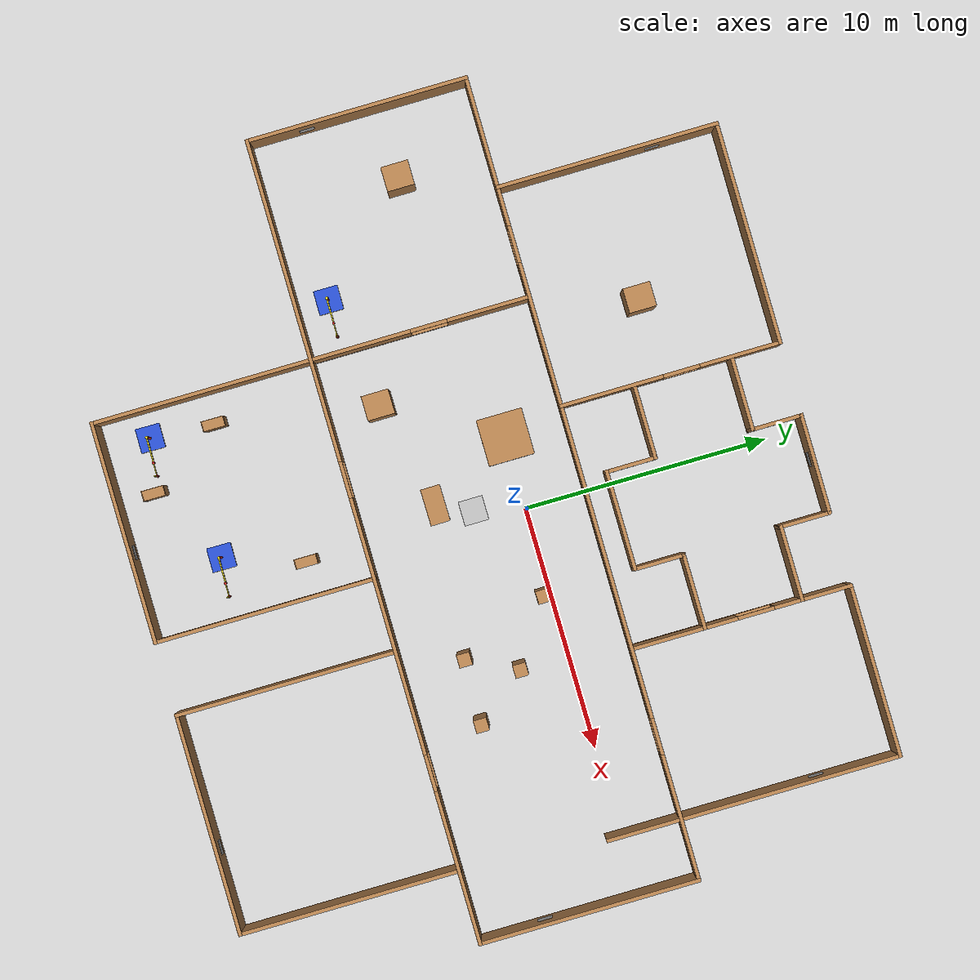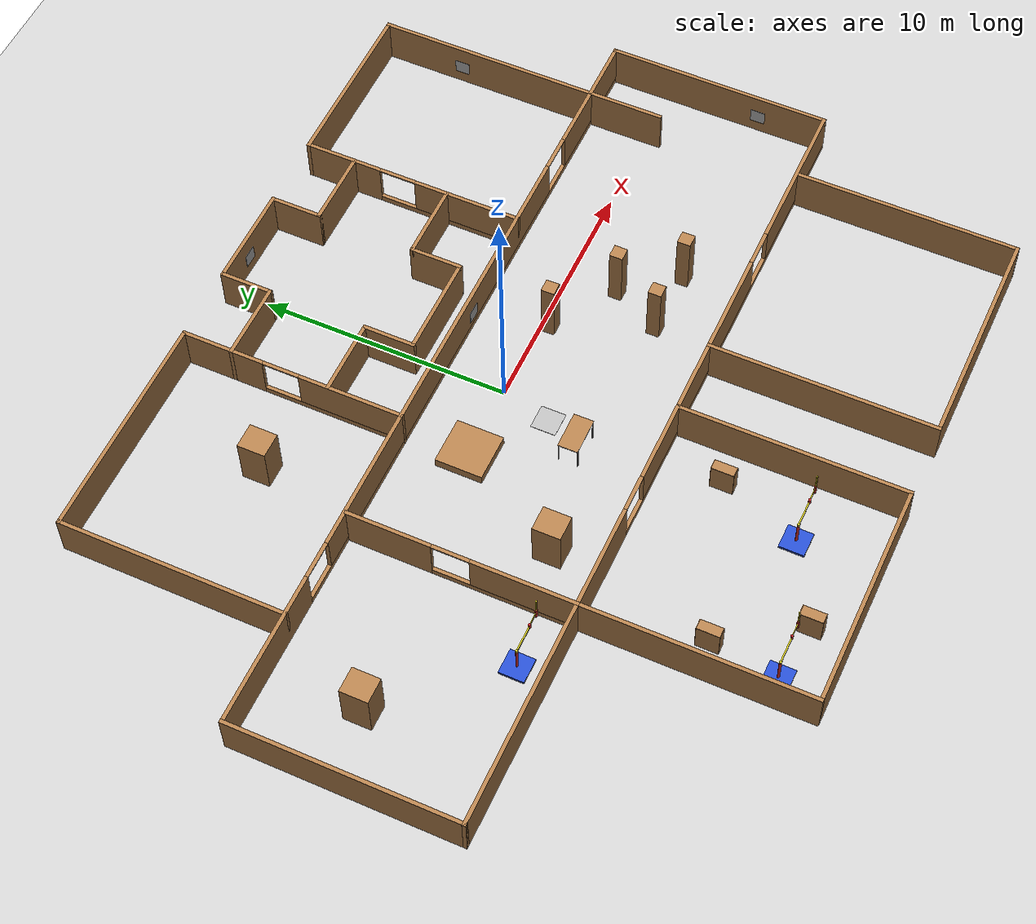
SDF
<sdf version="1.7">
 <world name="default">
  <light name="sun" type="directional">
   <pose>0 0 10 0 -0 0</pose>
   <diffuse>0.8 0.8 0.8 1</diffuse>
   <specular>0.2 0.2 0.2 1</specular>
   <attenuation>
    <range>1000</range>
    <constant>0.9</constant>
    <linear>0.01</linear>
    <quadratic>0.001</quadratic>
   </attenuation>
   <direction>-0.5 0.1 -0.9</direction>
   <spot><inner_angle>0</inner_angle><outer_angle>0</outer_angle><falloff>0</falloff></spot>
  </light>
  <model name="ground_plane">
   <static>1</static>
   <link name="link">
    <collision name="collision">
     <geometry><plane><normal>0 0 1</normal><size>25 25</size></plane></geometry>
     <surface><friction><ode><mu>100</mu><mu2>50</mu2></ode></friction></surface>
    </collision>
    <visual name="visual">
     <cast_shadows>0</cast_shadows>
     <geometry><plane><normal>0 0 1</normal><size>25 25</size></plane></geometry>
     <material>
      <script><uri>file://media/materials/scripts/gazebo.material</uri><name>Gazebo/Grey</name></script>
     </material>
    </visual>
   </link>
  </model>
  <gravity>0 0 -9.8</gravity>
  <magnetic_field>6e-06 2.3e-05 -4.2e-05</magnetic_field>
  <atmosphere type="adiabatic"/>
  <plugin name="ros_interface_plugin" filename="librotors_gazebo_ros_interface_plugin.so"/>
  <physics name="default_physics" default="0" type="ode">
   <max_step_size>0.001</max_step_size>
   <real_time_factor>1</real_time_factor>
   <real_time_update_rate>1000</real_time_update_rate>
  </physics>
  <scene>
   <sky><clouds><speed>30</speed></clouds><sunrise>5</sunrise><time>10</time><sunset>15</sunset></sky>
   <ambient>0.5 0.5 0.5 1</ambient>
   <background>0.7 0.7 0.7 1</background>
   <shadows>1</shadows>
  </scene>
  <spherical_coordinates>
   <surface_model>EARTH_WGS84</surface_model>
   <latitude_deg>0</latitude_deg>
   <longitude_deg>0</longitude_deg>
   <elevation>0</elevation>
   <heading_deg>0</heading_deg>
  </spherical_coordinates>
  <model name="table">
   <static>0</static>
   <link name="link">
    <collision name="surface">
     <pose>0 0 1 0 -0 0</pose>
     <geometry><box><size>1.5 0.8 0.03</size></box></geometry>
     <surface><friction><ode><mu>0.6</mu><mu2>0.6</mu2></ode></friction></surface>
    </collision>
    <visual name="visual1">
     <pose>0 0 1 0 -0 0</pose>
     <geometry><box><size>1.5 0.8 0.03</size></box></geometry>
     <material>
      <script><uri>file://media/materials/scripts/gazebo.material</uri><name>Gazebo/Wood</name></script>
     </material>
    </visual>
    <collision name="front_left_leg">
     <pose>0.68 0.38 0.5 0 -0 0</pose>
     <geometry><cylinder><radius>0.02</radius><length>1</length></cylinder></geometry>
    </collision>
    <visual name="front_left_leg">
     <pose>0.68 0.38 0.5 0 -0 0</pose>
     <geometry><cylinder><radius>0.02</radius><length>1</length></cylinder></geometry>
     <material>
      <script><uri>file://media/materials/scripts/gazebo.material</uri><name>Gazebo/Grey</name></script>
     </material>
    </visual>
    <collision name="front_right_leg">
     <pose>0.68 -0.38 0.5 0 -0 0</pose>
     <geometry><cylinder><radius>0.02</radius><length>1</length></cylinder></geometry>
    </collision>
    <visual name="front_right_leg">
     <pose>0.68 -0.38 0.5 0 -0 0</pose>
     <geometry><cylinder><radius>0.02</radius><length>1</length></cylinder></geometry>
     <material>
      <script><uri>file://media/materials/scripts/gazebo.material</uri><name>Gazebo/Grey</name></script>
     </material>
    </visual>
    <collision name="back_right_leg">
     <pose>-0.68 -0.38 0.5 0 -0 0</pose>
     <geometry><cylinder><radius>0.02</radius><length>1</length></cylinder></geometry>
    </collision>
    <visual name="back_right_leg">
     <pose>-0.68 -0.38 0.5 0 -0 0</pose>
     <geometry><cylinder><radius>0.02</radius><length>1</length></cylinder></geometry>
     <material>
      <script><uri>file://media/materials/scripts/gazebo.material</uri><name>Gazebo/Grey</name></script>
     </material>
    </visual>
    <collision name="back_left_leg">
     <pose>-0.68 0.38 0.5 0 -0 0</pose>
     <geometry><cylinder><radius>0.02</radius><length>1</length></cylinder></geometry>
    </collision>
    <visual name="back_left_leg">
     <pose>-0.68 0.38 0.5 0 -0 0</pose>
     <geometry><cylinder><radius>0.02</radius><length>1</length></cylinder></geometry>
     <material>
      <script><uri>file://media/materials/scripts/gazebo.material</uri><name>Gazebo/Grey</name></script>
     </material>
    </visual>
    <inertial>
     <inertia><ixx>1</ixx><ixy>0</ixy><ixz>0</ixz><iyy>1</iyy><iyz>0</iyz><izz>1</izz></inertia>
     <mass>1</mass>
    </inertial>
   </link>
   <pose>-1.15242 -3.43978 -2.2e-05 2e-06 3e-06 0.008082</pose>
  </model>
  <model name="unit_box_0">
   <pose>-2.99922 0.000744 0.193607 5e-06 -0 -0.000955</pose>
   <link name="link">
    <inertial>
     <mass>1</mass>
     <inertia>
      <ixx>0.166667</ixx>
      <ixy>0</ixy>
      <ixz>0</ixz>
      <iyy>0.166667</iyy>
      <iyz>0</iyz>
      <izz>0.166667</izz>
     </inertia>
    </inertial>
    <collision name="collision"><geometry><box><size>1.90824 1.89174 0.387223</size></box></geometry></collision>
    <visual name="visual">
     <geometry><box><size>1.90824 1.89174 0.387223</size></box></geometry>
     <material>
      <script><uri>file://media/materials/scripts/gazebo.material</uri><name>Gazebo/Wood</name></script>
     </material>
    </visual>
   </link>
   <static>0</static>
  </model>
  <model name="unit_box_0_clone">
   <pose>3.46103 -0.330294 1.29125 1e-06 -1e-06 0.012908</pose>
   <link name="link">
    <inertial>
     <mass>1</mass>
     <inertia>
      <ixx>0.166667</ixx>
      <ixy>0</ixy>
      <ixz>0</ixz>
      <iyy>0.166667</iyy>
      <iyz>0</iyz>
      <izz>0.166667</izz>
     </inertia>
    </inertial>
    <collision name="collision"><geometry><box><size>0.52404 0.528614 2.5825</size></box></geometry></collision>
    <visual name="visual">
     <geometry><box><size>0.52404 0.528614 2.5825</size></box></geometry>
     <material>
      <script><uri>file://media/materials/scripts/gazebo.material</uri><name>Gazebo/Wood</name></script>
     </material>
    </visual>
   </link>
   <static>0</static>
  </model>
  <model name="unit_box_0_clone_3">
   <pose>7.64647 -4.07673 1.29125 -1e-06 1e-06 -7.9e-05</pose>
   <link name="link">
    <inertial>
     <mass>1</mass>
     <inertia>
      <ixx>0.166667</ixx>
      <ixy>0</ixy>
      <ixz>0</ixz>
      <iyy>0.166667</iyy>
      <iyz>0</iyz>
      <izz>0.166667</izz>
     </inertia>
    </inertial>
    <collision name="collision"><geometry><box><size>0.52404 0.528614 2.5825</size></box></geometry></collision>
    <visual name="visual">
     <geometry><box><size>0.52404 0.528614 2.5825</size></box></geometry>
     <material>
      <script><uri>file://media/materials/scripts/gazebo.material</uri><name>Gazebo/Wood</name></script>
     </material>
    </visual>
   </link>
   <static>0</static>
  </model>
  <model name="static_apriltag_0">
   <link name="link">
    <pose>0 0 0 0 1.57 0</pose>
    <inertial>
     <mass>0.39</mass>
     <inertia><ixx>0.00058</ixx><ixy>0</ixy><ixz>0</ixz><iyy>0.00058</iyy><iyz>0</iyz><izz>0.00019</izz></inertia>
    </inertial>
    <collision name="collision"><geometry><box><size>0.6 0.6 0.01</size></box></geometry></collision>
    <visual name="visual">
     <geometry><box><size>0.6 0.6 0.01</size></box></geometry>
     <material>
      <script>
       <uri>model://apriltag/materials/scripts</uri>
       <uri>model://apriltag/materials/textures</uri>
       <name>apriltag/Diffuse0</name>
      </script>
     </material>
    </visual>
    <gravity>0</gravity>
   </link>
   <pose>1.24802 11.3597 0.8 -1e-06 0.001593 1.57</pose>
   <static>1</static>
   <pose>1.90787 0.108649 0 0 -0 0</pose>
  </model>
  <model name="static_apriltag_1">
   <link name="link">
    <pose>0 0 0 0 1.57 0</pose>
    <inertial>
     <mass>0.39</mass>
     <inertia><ixx>0.00058</ixx><ixy>0</ixy><ixz>0</ixz><iyy>0.00058</iyy><iyz>0</iyz><izz>0.00019</izz></inertia>
    </inertial>
    <collision name="collision"><geometry><box><size>0.6 0.6 0.01</size></box></geometry></collision>
    <visual name="visual">
     <geometry><box><size>0.6 0.6 0.01</size></box></geometry>
     <material>
      <script>
       <uri>model://apriltag/materials/scripts</uri>
       <uri>model://apriltag/materials/textures</uri>
       <name>apriltag/Diffuse1</name>
      </script>
     </material>
    </visual>
    <gravity>0</gravity>
   </link>
   <pose>2.36051 2.3558 0.799352 0.000796 0.000796 -1.57</pose>
   <static>1</static>
   <pose>1.36256 0.459264 0 0 -0 0</pose>
  </model>
  <model name="static_apriltag_2">
   <link name="link">
    <pose>0 0 0 0 1.57 0</pose>
    <inertial>
     <mass>0.39</mass>
     <inertia><ixx>0.00058</ixx><ixy>0</ixy><ixz>0</ixz><iyy>0.00058</iyy><iyz>0</iyz><izz>0.00019</izz></inertia>
    </inertial>
    <collision name="collision"><geometry><box><size>0.6 0.6 0.01</size></box></geometry></collision>
    <visual name="visual">
     <geometry><box><size>0.6 0.6 0.01</size></box></geometry>
     <material>
      <script>
       <uri>model://apriltag/materials/scripts</uri>
       <uri>model://apriltag/materials/textures</uri>
       <name>apriltag/Diffuse2</name>
      </script>
     </material>
    </visual>
    <gravity>0</gravity>
   </link>
   <pose>13.3997 8.11372 0.799999 -1e-06 0.001593 -0.003185</pose>
   <static>1</static>
   <pose>0.80811 0.829943 0 0 -0 0</pose>
  </model>
  <model name="static_apriltag_3">
   <link name="link">
    <pose>0 0 0 -1.57 1.57 -0</pose>
    <inertial>
     <mass>0.39</mass>
     <inertia><ixx>0.00058</ixx><ixy>0</ixy><ixz>0</ixz><iyy>0.00058</iyy><iyz>0</iyz><izz>0.00019</izz></inertia>
    </inertial>
    <collision name="collision"><geometry><box><size>0.6 0.6 0.01</size></box></geometry></collision>
    <visual name="visual">
     <geometry><box><size>0.6 0.6 0.01</size></box></geometry>
     <material>
      <script>
       <uri>model://apriltag/materials/scripts</uri>
       <uri>model://apriltag/materials/textures</uri>
       <name>apriltag/Diffuse3</name>
      </script>
     </material>
    </visual>
    <gravity>0</gravity>
   </link>
   <pose>15.8894 -3.83423 0.8 3.14159 -0 -1.57159</pose>
   <static>1</static>
   <pose>3.65849 3.02317 0 0 -0 0</pose>
  </model>
  <model name="static_apriltag_4">
   <link name="link">
    <pose>0 0 0 0 1.57 0</pose>
    <inertial>
     <mass>0.39</mass>
     <inertia><ixx>0.00058</ixx><ixy>0</ixy><ixz>0</ixz><iyy>0.00058</iyy><iyz>0</iyz><izz>0.00019</izz></inertia>
    </inertial>
    <collision name="collision"><geometry><box><size>0.6 0.6 0.01</size></box></geometry></collision>
    <visual name="visual">
     <geometry><box><size>0.6 0.6 0.01</size></box></geometry>
     <material>
      <script>
       <uri>model://apriltag/materials/scripts</uri>
       <uri>model://apriltag/materials/textures</uri>
       <name>apriltag/Diffuse4</name>
      </script>
     </material>
    </visual>
    <gravity>0</gravity>
   </link>
   <pose>9.54746 -15.4586 0.8 0 0 -1.57</pose>
   <static>1</static>
   <pose>3.93537 3.29316 0 0 -0 0</pose>
  </model>
  <model name="static_apriltag_5">
   <link name="link">
    <pose>0 0 0 -1.57 1.57 -0</pose>
    <inertial>
     <mass>0.39</mass>
     <inertia><ixx>0.00058</ixx><ixy>0</ixy><ixz>0</ixz><iyy>0.00058</iyy><iyz>0</iyz><izz>0.00019</izz></inertia>
    </inertial>
    <collision name="collision"><geometry><box><size>0.6 0.6 0.01</size></box></geometry></collision>
    <visual name="visual">
     <geometry><box><size>0.6 0.6 0.01</size></box></geometry>
     <material>
      <script>
       <uri>model://apriltag/materials/scripts</uri>
       <uri>model://apriltag/materials/textures</uri>
       <name>apriltag/Diffuse5</name>
      </script>
     </material>
    </visual>
    <gravity>0</gravity>
   </link>
   <pose>-2.68152 -15.4682 0.800624 0.000796 0.000796 1e-06</pose>
   <static>1</static>
   <pose>5.04082 3.71574 0 0 -0 0</pose>
  </model>
  <model name="static_apriltag_6">
   <link name="link">
    <pose>0 0 0 -1.57 1.57 -0</pose>
    <inertial>
     <mass>0.39</mass>
     <inertia><ixx>0.00058</ixx><ixy>0</ixy><ixz>0</ixz><iyy>0.00058</iyy><iyz>0</iyz><izz>0.00019</izz></inertia>
    </inertial>
    <collision name="collision"><geometry><box><size>0.6 0.6 0.01</size></box></geometry></collision>
    <visual name="visual">
     <geometry><box><size>0.6 0.6 0.01</size></box></geometry>
     <material>
      <script>
       <uri>model://apriltag/materials/scripts</uri>
       <uri>model://apriltag/materials/textures</uri>
       <name>apriltag/Diffuse6</name>
      </script>
     </material>
    </visual>
    <gravity>0</gravity>
   </link>
   <pose>-16.9496 -4.18033 0.799599 -0.000796 0.000796 -1.57</pose>
   <static>1</static>
   <pose>3.43144 4.34187 0 0 -0 0</pose>
  </model>
  <model name="static_apriltag_7">
   <link name="link">
    <inertial>
     <mass>0.39</mass>
     <inertia><ixx>0.00058</ixx><ixy>0</ixy><ixz>0</ixz><iyy>0.00058</iyy><iyz>0</iyz><izz>0.00019</izz></inertia>
    </inertial>
    <collision name="collision"><geometry><box><size>0.6 0.6 0.01</size></box></geometry></collision>
    <visual name="visual">
     <geometry><box><size>0.6 0.6 0.01</size></box></geometry>
     <material>
      <script>
       <uri>model://apriltag/materials/scripts</uri>
       <uri>model://apriltag/materials/textures</uri>
       <name>apriltag/Diffuse7</name>
      </script>
     </material>
    </visual>
    <gravity>0</gravity>
   </link>
   <pose>-12.4497 8.83016 0.8 1.57 -0 1.57</pose>
   <static>1</static>
   <pose>3.12393 4.47604 0 0 -0 0</pose>
  </model>
  <model name="simple_arm">
   <link name="arm_base">
    <inertial>
     <pose>0 0 0.00099 0 -0 0</pose>
     <inertia><ixx>1.11</ixx><ixy>0</ixy><ixz>0</ixz><iyy>100.11</iyy><iyz>0</iyz><izz>1.01</izz></inertia>
     <mass>101</mass>
    </inertial>
    <collision name="arm_base_geom">
     <pose>0 0 0.05 0 -0 0</pose>
     <geometry><box><size>1 1 0.1</size></box></geometry>
    </collision>
    <visual name="arm_base_geom_visual">
     <pose>0 0 0.05 0 -0 0</pose>
     <geometry><box><size>1 1 0.1</size></box></geometry>
     <material>
      <script><uri>file://media/materials/scripts/gazebo.material</uri><name>Gazebo/Blue</name></script>
     </material>
    </visual>
    <collision name="arm_base_geom_arm_trunk">
     <pose>0 0 0.6 0 -0 0</pose>
     <geometry><cylinder><radius>0.05</radius><length>1</length></cylinder></geometry>
    </collision>
    <visual name="arm_base_geom_arm_trunk_visual">
     <pose>0 0 0.6 0 -0 0</pose>
     <geometry><cylinder><radius>0.05</radius><length>1</length></cylinder></geometry>
     <material>
      <script><uri>file://media/materials/scripts/gazebo.material</uri><name>Gazebo/Red</name></script>
     </material>
    </visual>
   </link>
   <link name="arm_shoulder_pan">
    <pose>0 0 1.1 0 -0 0</pose>
    <inertial>
     <pose>0.045455 0 0 0 -0 0</pose>
     <inertia><ixx>0.011</ixx><ixy>0</ixy><ixz>0</ixz><iyy>0.0225</iyy><iyz>0</iyz><izz>0.0135</izz></inertia>
     <mass>1.1</mass>
    </inertial>
    <collision name="arm_shoulder_pan_geom">
     <pose>0 0 0.05 0 -0 0</pose>
     <geometry><cylinder><radius>0.05</radius><length>0.1</length></cylinder></geometry>
    </collision>
    <visual name="arm_shoulder_pan_geom_visual">
     <pose>0 0 0.05 0 -0 0</pose>
     <geometry><cylinder><radius>0.05</radius><length>0.1</length></cylinder></geometry>
     <material>
      <script><uri>file://media/materials/scripts/gazebo.material</uri><name>Gazebo/Yellow</name></script>
     </material>
    </visual>
    <collision name="arm_shoulder_pan_geom_arm_shoulder">
     <pose>0.55 0 0.05 0 -0 0</pose>
     <geometry><box><size>1 0.05 0.1</size></box></geometry>
    </collision>
    <visual name="arm_shoulder_pan_geom_arm_shoulder_visual">
     <pose>0.55 0 0.05 0 -0 0</pose>
     <geometry><box><size>1 0.05 0.1</size></box></geometry>
     <material>
      <script><uri>file://media/materials/scripts/gazebo.material</uri><name>Gazebo/Yellow</name></script>
     </material>
    </visual>
   </link>
   <link name="arm_elbow_pan">
    <pose>1.05 0 1.1 0 -0 0</pose>
    <inertial>
     <pose>0.0875 0 0.083333 0 -0 0</pose>
     <inertia>
      <ixx>0.031</ixx>
      <ixy>0</ixy>
      <ixz>0.005</ixz>
      <iyy>0.07275</iyy>
      <iyz>0</iyz>
      <izz>0.04475</izz>
     </inertia>
     <mass>1.2</mass>
    </inertial>
    <collision name="arm_elbow_pan_geom">
     <pose>0 0 0.1 0 -0 0</pose>
     <geometry><cylinder><radius>0.05</radius><length>0.2</length></cylinder></geometry>
    </collision>
    <visual name="arm_elbow_pan_geom_visual">
     <pose>0 0 0.1 0 -0 0</pose>
     <geometry><cylinder><radius>0.05</radius><length>0.2</length></cylinder></geometry>
     <material>
      <script><uri>file://media/materials/scripts/gazebo.material</uri><name>Gazebo/Red</name></script>
     </material>
    </visual>
    <collision name="arm_elbow_pan_geom_arm_elbow">
     <pose>0.3 0 0.15 0 -0 0</pose>
     <geometry><box><size>0.5 0.03 0.1</size></box></geometry>
    </collision>
    <visual name="arm_elbow_pan_geom_arm_elbow_visual">
     <pose>0.3 0 0.15 0 -0 0</pose>
     <geometry><box><size>0.5 0.03 0.1</size></box></geometry>
     <material>
      <script><uri>file://media/materials/scripts/gazebo.material</uri><name>Gazebo/Yellow</name></script>
     </material>
    </visual>
    <collision name="arm_elbow_pan_geom_arm_wrist">
     <pose>0.55 0 0.15 0 -0 0</pose>
     <geometry><cylinder><radius>0.05</radius><length>0.3</length></cylinder></geometry>
    </collision>
    <visual name="arm_elbow_pan_geom_arm_wrist_visual">
     <pose>0.55 0 0.15 0 -0 0</pose>
     <geometry><cylinder><radius>0.05</radius><length>0.3</length></cylinder></geometry>
     <material>
      <script><uri>file://media/materials/scripts/gazebo.material</uri><name>Gazebo/Red</name></script>
     </material>
    </visual>
   </link>
   <link name="arm_wrist_lift">
    <pose>1.6 0 1.05 0 -0 0</pose>
    <inertial>
     <inertia><ixx>0.01</ixx><ixy>0</ixy><ixz>0</ixz><iyy>0.01</iyy><iyz>0</iyz><izz>0.001</izz></inertia>
     <mass>0.1</mass>
    </inertial>
    <collision name="arm_wrist_lift_geom">
     <pose>0 0 0.5 0 -0 0</pose>
     <geometry><cylinder><radius>0.03</radius><length>1</length></cylinder></geometry>
    </collision>
    <visual name="arm_wrist_lift_geom_visual">
     <pose>0 0 0.5 0 -0 0</pose>
     <geometry><cylinder><radius>0.03</radius><length>1</length></cylinder></geometry>
     <material>
      <script><uri>file://media/materials/scripts/gazebo.material</uri><name>Gazebo/Yellow</name></script>
     </material>
    </visual>
   </link>
   <link name="arm_wrist_roll">
    <pose>1.6 0 1 0 -0 0</pose>
    <inertial>
     <inertia><ixx>0.01</ixx><ixy>0</ixy><ixz>0</ixz><iyy>0.01</iyy><iyz>0</iyz><izz>0.001</izz></inertia>
     <mass>0.1</mass>
    </inertial>
    <collision name="arm_wrist_roll_geom">
     <pose>0 0 0.025 0 -0 0</pose>
     <geometry><cylinder><radius>0.05</radius><length>0.05</length></cylinder></geometry>
    </collision>
    <visual name="arm_wrist_roll_geom_visual">
     <pose>0 0 0.025 0 -0 0</pose>
     <geometry><cylinder><radius>0.05</radius><length>0.05</length></cylinder></geometry>
     <material>
      <script><uri>file://media/materials/scripts/gazebo.material</uri><name>Gazebo/Red</name></script>
     </material>
    </visual>
   </link>
   <joint name="arm_shoulder_pan_joint" type="revolute">
    <parent>arm_base</parent>
    <child>arm_shoulder_pan</child>
    <axis>
     <dynamics>
      <damping>1</damping>
      <friction>0</friction>
      <spring_reference>0</spring_reference>
      <spring_stiffness>0</spring_stiffness>
     </dynamics>
     <xyz expressed_in="__model__">0 0 1</xyz>
     <limit><lower>-1e+16</lower><upper>1e+16</upper></limit>
    </axis>
   </joint>
   <joint name="arm_elbow_pan_joint" type="revolute">
    <parent>arm_shoulder_pan</parent>
    <child>arm_elbow_pan</child>
    <axis>
     <dynamics>
      <damping>1</damping>
      <friction>0</friction>
      <spring_reference>0</spring_reference>
      <spring_stiffness>0</spring_stiffness>
     </dynamics>
     <xyz expressed_in="__model__">0 0 1</xyz>
     <limit><lower>-1e+16</lower><upper>1e+16</upper></limit>
    </axis>
   </joint>
   <joint name="arm_wrist_lift_joint" type="prismatic">
    <parent>arm_elbow_pan</parent>
    <child>arm_wrist_lift</child>
    <axis>
     <dynamics>
      <damping>1</damping>
      <friction>0</friction>
      <spring_reference>0</spring_reference>
      <spring_stiffness>0</spring_stiffness>
     </dynamics>
     <limit><lower>-0.8</lower><upper>0.1</upper></limit>
     <xyz expressed_in="__model__">0 0 1</xyz>
    </axis>
   </joint>
   <joint name="arm_wrist_roll_joint" type="revolute">
    <parent>arm_wrist_lift</parent>
    <child>arm_wrist_roll</child>
    <axis>
     <dynamics>
      <damping>1</damping>
      <friction>0</friction>
      <spring_reference>0</spring_reference>
      <spring_stiffness>0</spring_stiffness>
     </dynamics>
     <limit><lower>-2.99999</lower><upper>2.99999</upper></limit>
     <xyz expressed_in="__model__">0 0 1</xyz>
    </axis>
   </joint>
   <pose>-10.2605 -5.28171 -0 0 -0 -0.006475</pose>
  </model>
  <model name="0810_MAP1_elment1">
   <pose>-0.522667 -2.05085 0 0 -0 0</pose>
   <link name="Wall_0">
    <pose>0 -4.5 0 0 -0 0</pose>
    <visual name="Wall_0_Visual_0">
     <pose>-9.94707 0 0.9 0 -0 0</pose>
     <geometry><box><size>13.2559 0.15 1.8</size></box></geometry>
     <material>
      <script><uri>file://media/materials/scripts/gazebo.material</uri><name>Gazebo/Wood</name></script>
      <ambient>1 1 1 1</ambient>
     </material>
     <meta><layer>0</layer></meta>
    </visual>
    <collision name="Wall_0_Collision_0">
     <geometry><box><size>13.2559 0.15 1.8</size></box></geometry>
     <pose>-9.94707 0 0.9 0 -0 0</pose>
    </collision>
    <visual name="Wall_0_Visual_1">
     <pose>6.62793 0 0.125 0 -0 0</pose>
     <geometry><box><size>19.8941 0.15 0.25</size></box></geometry>
     <material>
      <script><uri>file://media/materials/scripts/gazebo.material</uri><name>Gazebo/Wood</name></script>
      <ambient>1 1 1 1</ambient>
     </material>
     <meta><layer>0</layer></meta>
    </visual>
    <collision name="Wall_0_Collision_1">
     <geometry><box><size>19.8941 0.15 0.25</size></box></geometry>
     <pose>6.62793 0 0.125 0 -0 0</pose>
    </collision>
    <visual name="Wall_0_Visual_2">
     <pose>3.45691 0 1.025 0 -0 0</pose>
     <geometry><box><size>10.5521 0.15 1.55</size></box></geometry>
     <material>
      <script><uri>file://media/materials/scripts/gazebo.material</uri><name>Gazebo/Wood</name></script>
      <ambient>1 1 1 1</ambient>
     </material>
     <meta><layer>0</layer></meta>
    </visual>
    <collision name="Wall_0_Collision_2">
     <geometry><box><size>10.5521 0.15 1.55</size></box></geometry>
     <pose>3.45691 0 1.025 0 -0 0</pose>
    </collision>
    <visual name="Wall_0_Visual_3">
     <pose>13.404 0 1.025 0 -0 0</pose>
     <geometry><box><size>6.34204 0.15 1.55</size></box></geometry>
     <material>
      <script><uri>file://media/materials/scripts/gazebo.material</uri><name>Gazebo/Wood</name></script>
      <ambient>1 1 1 1</ambient>
     </material>
     <meta><layer>0</layer></meta>
    </visual>
    <collision name="Wall_0_Collision_3">
     <geometry><box><size>6.34204 0.15 1.55</size></box></geometry>
     <pose>13.404 0 1.025 0 -0 0</pose>
    </collision>
    <visual name="Wall_0_Visual_4">
     <pose>-2.56915 0 1.775 0 -0 0</pose>
     <geometry><box><size>1.5 0.15 0.05</size></box></geometry>
     <material>
      <script><uri>file://media/materials/scripts/gazebo.material</uri><name>Gazebo/Wood</name></script>
      <ambient>1 1 1 1</ambient>
     </material>
     <meta><layer>0</layer></meta>
    </visual>
    <collision name="Wall_0_Collision_4">
     <geometry><box><size>1.5 0.15 0.05</size></box></geometry>
     <pose>-2.56915 0 1.775 0 -0 0</pose>
    </collision>
    <visual name="Wall_0_Visual_5">
     <pose>9.48296 0 1.775 0 -0 0</pose>
     <geometry><box><size>1.5 0.15 0.05</size></box></geometry>
     <material>
      <script><uri>file://media/materials/scripts/gazebo.material</uri><name>Gazebo/Wood</name></script>
      <ambient>1 1 1 1</ambient>
     </material>
     <meta><layer>0</layer></meta>
    </visual>
    <collision name="Wall_0_Collision_5">
     <geometry><box><size>1.5 0.15 0.05</size></box></geometry>
     <pose>9.48296 0 1.775 0 -0 0</pose>
    </collision>
   </link>
   <link name="Wall_12">
    <collision name="Wall_12_Collision">
     <geometry><box><size>9.15 0.15 1.8</size></box></geometry>
     <pose>0 0 0.9 0 -0 0</pose>
    </collision>
    <visual name="Wall_12_Visual">
     <pose>0 0 0.9 0 -0 0</pose>
     <geometry><box><size>9.15 0.15 1.8</size></box></geometry>
     <material>
      <script><uri>file://media/materials/scripts/gazebo.material</uri><name>Gazebo/Wood</name></script>
      <ambient>1 1 1 1</ambient>
     </material>
     <meta><layer>0</layer></meta>
    </visual>
    <pose>-3 -13.5 0 0 -0 0</pose>
   </link>
   <link name="Wall_14">
    <collision name="Wall_14_Collision">
     <geometry><box><size>9.15 0.15 1.8</size></box></geometry>
     <pose>0 0 0.9 0 -0 0</pose>
    </collision>
    <visual name="Wall_14_Visual">
     <pose>0 0 0.9 0 -0 0</pose>
     <geometry><box><size>9.15 0.15 1.8</size></box></geometry>
     <material>
      <script><uri>file://media/materials/scripts/gazebo.material</uri><name>Gazebo/Wood</name></script>
      <ambient>1 1 1 1</ambient>
     </material>
     <meta><layer>0</layer></meta>
    </visual>
    <pose>1.5 -9 0 0 -0 1.5708</pose>
   </link>
   <link name="Wall_17">
    <collision name="Wall_17_Collision">
     <geometry><box><size>9.15 0.15 1.8</size></box></geometry>
     <pose>0 0 0.9 0 -0 0</pose>
    </collision>
    <visual name="Wall_17_Visual">
     <pose>0 0 0.9 0 -0 0</pose>
     <geometry><box><size>9.15 0.15 1.8</size></box></geometry>
     <material>
      <script><uri>file://media/materials/scripts/gazebo.material</uri><name>Gazebo/Wood</name></script>
      <ambient>1 1 1 1</ambient>
     </material>
     <meta><layer>0</layer></meta>
    </visual>
    <pose>4.5 -9 0 0 -0 -1.5708</pose>
   </link>
   <link name="Wall_19">
    <collision name="Wall_19_Collision">
     <geometry><box><size>9.15 0.15 1.8</size></box></geometry>
     <pose>0 0 0.9 0 -0 0</pose>
    </collision>
    <visual name="Wall_19_Visual">
     <pose>0 0 0.9 0 -0 0</pose>
     <geometry><box><size>9.15 0.15 1.8</size></box></geometry>
     <material>
      <script><uri>file://media/materials/scripts/gazebo.material</uri><name>Gazebo/Wood</name></script>
      <ambient>1 1 1 1</ambient>
     </material>
     <meta><layer>0</layer></meta>
    </visual>
    <pose>9 -13.5 0 0 -0 0</pose>
   </link>
   <link name="Wall_2">
    <collision name="Wall_2_Collision">
     <geometry><box><size>9.15 0.15 1.8</size></box></geometry>
     <pose>0 0 0.9 0 -0 0</pose>
    </collision>
    <visual name="Wall_2_Visual">
     <pose>0 0 0.9 0 -0 0</pose>
     <geometry><box><size>9.15 0.15 1.8</size></box></geometry>
     <material>
      <script><uri>file://media/materials/scripts/gazebo.material</uri><name>Gazebo/Wood</name></script>
      <ambient>1 1 1 1</ambient>
     </material>
     <meta><layer>0</layer></meta>
    </visual>
    <pose>-16.5 0 0 0 -0 1.5708</pose>
   </link>
   <link name="Wall_21">
    <collision name="Wall_21_Collision">
     <geometry><box><size>9.15 0.15 1.8</size></box></geometry>
     <pose>0 0 0.9 0 -0 0</pose>
    </collision>
    <visual name="Wall_21_Visual">
     <pose>0 0 0.9 0 -0 0</pose>
     <geometry><box><size>9.15 0.15 1.8</size></box></geometry>
     <material>
      <script><uri>file://media/materials/scripts/gazebo.material</uri><name>Gazebo/Wood</name></script>
      <ambient>1 1 1 1</ambient>
     </material>
     <meta><layer>0</layer></meta>
    </visual>
    <pose>13.5 -9 0 0 -0 1.5708</pose>
   </link>
   <link name="Wall_23">
    <collision name="Wall_23_Collision">
     <geometry><box><size>9.15 0.15 1.8</size></box></geometry>
     <pose>0 0 0.9 0 -0 0</pose>
    </collision>
    <visual name="Wall_23_Visual">
     <pose>0 0 0.9 0 -0 0</pose>
     <geometry><box><size>9.15 0.15 1.8</size></box></geometry>
     <material>
      <script><uri>file://media/materials/scripts/gazebo.material</uri><name>Gazebo/Wood</name></script>
      <ambient>1 1 1 1</ambient>
     </material>
     <meta><layer>0</layer></meta>
    </visual>
    <pose>16.5 0 0 0 -0 1.5708</pose>
   </link>
   <link name="Wall_25">
    <collision name="Wall_25_Collision">
     <geometry><box><size>9.15 0.15 1.8</size></box></geometry>
     <pose>0 0 0.9 0 -0 0</pose>
    </collision>
    <visual name="Wall_25_Visual">
     <pose>0 0 0.9 0 -0 0</pose>
     <geometry><box><size>9.15 0.15 1.8</size></box></geometry>
     <material>
      <script><uri>file://media/materials/scripts/gazebo.material</uri><name>Gazebo/Wood</name></script>
      <ambient>1 1 1 1</ambient>
     </material>
     <meta><layer>0</layer></meta>
    </visual>
    <pose>-12 9 0 0 -0 1.5708</pose>
   </link>
   <link name="Wall_27">
    <collision name="Wall_27_Collision">
     <geometry><box><size>9.15 0.15 1.8</size></box></geometry>
     <pose>0 0 0.9 0 -0 0</pose>
    </collision>
    <visual name="Wall_27_Visual">
     <pose>0 0 0.9 0 -0 0</pose>
     <geometry><box><size>9.15 0.15 1.8</size></box></geometry>
     <material>
      <script><uri>file://media/materials/scripts/gazebo.material</uri><name>Gazebo/Wood</name></script>
      <ambient>1 1 1 1</ambient>
     </material>
     <meta><layer>0</layer></meta>
    </visual>
    <pose>-7.5 13.5 0 0 -0 0</pose>
   </link>
   <link name="Wall_29">
    <pose>-3 9 0 0 -0 -1.5708</pose>
    <visual name="Wall_29_Visual_0">
     <pose>-2.88476 0 0.9 0 -0 0</pose>
     <geometry><box><size>3.38047 0.15 1.8</size></box></geometry>
     <material>
      <script><uri>file://media/materials/scripts/gazebo.material</uri><name>Gazebo/Wood</name></script>
      <ambient>1 1 1 1</ambient>
     </material>
     <meta><layer>0</layer></meta>
    </visual>
    <collision name="Wall_29_Collision_0">
     <geometry><box><size>3.38047 0.15 1.8</size></box></geometry>
     <pose>-2.88476 0 0.9 0 -0 0</pose>
    </collision>
    <visual name="Wall_29_Visual_1">
     <pose>1.69024 0 0.125 0 -0 0</pose>
     <geometry><box><size>5.76953 0.15 0.25</size></box></geometry>
     <material>
      <script><uri>file://media/materials/scripts/gazebo.material</uri><name>Gazebo/Wood</name></script>
      <ambient>1 1 1 1</ambient>
     </material>
     <meta><layer>0</layer></meta>
    </visual>
    <collision name="Wall_29_Collision_1">
     <geometry><box><size>5.76953 0.15 0.25</size></box></geometry>
     <pose>1.69024 0 0.125 0 -0 0</pose>
    </collision>
    <visual name="Wall_29_Visual_2">
     <pose>2.44024 0 1.025 0 -0 0</pose>
     <geometry><box><size>4.26953 0.15 1.55</size></box></geometry>
     <material>
      <script><uri>file://media/materials/scripts/gazebo.material</uri><name>Gazebo/Wood</name></script>
      <ambient>1 1 1 1</ambient>
     </material>
     <meta><layer>0</layer></meta>
    </visual>
    <collision name="Wall_29_Collision_2">
     <geometry><box><size>4.26953 0.15 1.55</size></box></geometry>
     <pose>2.44024 0 1.025 0 -0 0</pose>
    </collision>
    <visual name="Wall_29_Visual_3">
     <pose>-0.444526 0 1.775 0 -0 0</pose>
     <geometry><box><size>1.5 0.15 0.05</size></box></geometry>
     <material>
      <script><uri>file://media/materials/scripts/gazebo.material</uri><name>Gazebo/Wood</name></script>
      <ambient>1 1 1 1</ambient>
     </material>
     <meta><layer>0</layer></meta>
    </visual>
    <collision name="Wall_29_Collision_3">
     <geometry><box><size>1.5 0.15 0.05</size></box></geometry>
     <pose>-0.444526 0 1.775 0 -0 0</pose>
    </collision>
   </link>
   <link name="Wall_31">
    <collision name="Wall_31_Collision">
     <geometry><box><size>3.15 0.15 1.8</size></box></geometry>
     <pose>0 0 0.9 0 -0 0</pose>
    </collision>
    <visual name="Wall_31_Visual">
     <pose>0 0 0.9 0 -0 0</pose>
     <geometry><box><size>3.15 0.15 1.8</size></box></geometry>
     <material>
      <script><uri>file://media/materials/scripts/gazebo.material</uri><name>Gazebo/Wood</name></script>
      <ambient>1 1 1 1</ambient>
     </material>
     <meta><layer>0</layer></meta>
    </visual>
    <pose>-1.5 11.5 0 0 -0 0</pose>
   </link>
   <link name="Wall_33">
    <collision name="Wall_33_Collision">
     <geometry><box><size>3.15 0.15 1.8</size></box></geometry>
     <pose>0 0 0.9 0 -0 0</pose>
    </collision>
    <visual name="Wall_33_Visual">
     <pose>0 0 0.9 0 -0 0</pose>
     <geometry><box><size>3.15 0.15 1.8</size></box></geometry>
     <material>
      <script><uri>file://media/materials/scripts/gazebo.material</uri><name>Gazebo/Wood</name></script>
      <ambient>1 1 1 1</ambient>
     </material>
     <meta><layer>0</layer></meta>
    </visual>
    <pose>-1.5 7.5 0 0 -0 0</pose>
   </link>
   <link name="Wall_35">
    <collision name="Wall_35_Collision">
     <geometry><box><size>2.15 0.15 1.8</size></box></geometry>
     <pose>0 0 0.9 0 -0 0</pose>
    </collision>
    <visual name="Wall_35_Visual">
     <pose>0 0 0.9 0 -0 0</pose>
     <geometry><box><size>2.15 0.15 1.8</size></box></geometry>
     <material>
      <script><uri>file://media/materials/scripts/gazebo.material</uri><name>Gazebo/Wood</name></script>
      <ambient>1 1 1 1</ambient>
     </material>
     <meta><layer>0</layer></meta>
    </visual>
    <pose>0 6.5 0 0 -0 -1.5708</pose>
   </link>
   <link name="Wall_37">
    <collision name="Wall_37_Collision">
     <geometry><box><size>4.15 0.15 1.8</size></box></geometry>
     <pose>0 0 0.9 0 -0 0</pose>
    </collision>
    <visual name="Wall_37_Visual">
     <pose>0 0 0.9 0 -0 0</pose>
     <geometry><box><size>4.15 0.15 1.8</size></box></geometry>
     <material>
      <script><uri>file://media/materials/scripts/gazebo.material</uri><name>Gazebo/Wood</name></script>
      <ambient>1 1 1 1</ambient>
     </material>
     <meta><layer>0</layer></meta>
    </visual>
    <pose>2 5.5 0 0 -0 0</pose>
   </link>
   <link name="Wall_39">
    <collision name="Wall_39_Collision">
     <geometry><box><size>2.15 0.15 1.8</size></box></geometry>
     <pose>0 0 0.9 0 -0 0</pose>
    </collision>
    <visual name="Wall_39_Visual">
     <pose>0 0 0.9 0 -0 0</pose>
     <geometry><box><size>2.15 0.15 1.8</size></box></geometry>
     <material>
      <script><uri>file://media/materials/scripts/gazebo.material</uri><name>Gazebo/Wood</name></script>
      <ambient>1 1 1 1</ambient>
     </material>
     <meta><layer>0</layer></meta>
    </visual>
    <pose>4 6.5 0 0 -0 1.5708</pose>
   </link>
   <link name="Wall_4">
    <pose>0 4.5 0 0 -0 0</pose>
    <visual name="Wall_4_Visual_0">
     <pose>-13.4881 0 0.9 0 -0 0</pose>
     <geometry><box><size>6.17383 0.15 1.8</size></box></geometry>
     <material>
      <script><uri>file://media/materials/scripts/gazebo.material</uri><name>Gazebo/Wood</name></script>
      <ambient>1 1 1 1</ambient>
     </material>
     <meta><layer>0</layer></meta>
    </visual>
    <collision name="Wall_4_Collision_0">
     <geometry><box><size>6.17383 0.15 1.8</size></box></geometry>
     <pose>-13.4881 0 0.9 0 -0 0</pose>
    </collision>
    <visual name="Wall_4_Visual_1">
     <pose>3.08691 0 0.125 0 -0 0</pose>
     <geometry><box><size>26.9762 0.15 0.25</size></box></geometry>
     <material>
      <script><uri>file://media/materials/scripts/gazebo.material</uri><name>Gazebo/Wood</name></script>
      <ambient>1 1 1 1</ambient>
     </material>
     <meta><layer>0</layer></meta>
    </visual>
    <collision name="Wall_4_Collision_1">
     <geometry><box><size>26.9762 0.15 0.25</size></box></geometry>
     <pose>3.08691 0 0.125 0 -0 0</pose>
    </collision>
    <visual name="Wall_4_Visual_2">
     <pose>0.472751 0 1.025 0 -0 0</pose>
     <geometry><box><size>18.7478 0.15 1.55</size></box></geometry>
     <material>
      <script><uri>file://media/materials/scripts/gazebo.material</uri><name>Gazebo/Wood</name></script>
      <ambient>1 1 1 1</ambient>
     </material>
     <meta><layer>0</layer></meta>
    </visual>
    <collision name="Wall_4_Collision_2">
     <geometry><box><size>18.7478 0.15 1.55</size></box></geometry>
     <pose>0.472751 0 1.025 0 -0 0</pose>
    </collision>
    <visual name="Wall_4_Visual_3">
     <pose>13.9608 0 1.025 0 -0 0</pose>
     <geometry><box><size>5.22833 0.15 1.55</size></box></geometry>
     <material>
      <script><uri>file://media/materials/scripts/gazebo.material</uri><name>Gazebo/Wood</name></script>
      <ambient>1 1 1 1</ambient>
     </material>
     <meta><layer>0</layer></meta>
    </visual>
    <collision name="Wall_4_Collision_3">
     <geometry><box><size>5.22833 0.15 1.55</size></box></geometry>
     <pose>13.9608 0 1.025 0 -0 0</pose>
    </collision>
    <visual name="Wall_4_Visual_4">
     <pose>-9.65117 0 1.775 0 -0 0</pose>
     <geometry><box><size>1.5 0.15 0.05</size></box></geometry>
     <material>
      <script><uri>file://media/materials/scripts/gazebo.material</uri><name>Gazebo/Wood</name></script>
      <ambient>1 1 1 1</ambient>
     </material>
     <meta><layer>0</layer></meta>
    </visual>
    <collision name="Wall_4_Collision_4">
     <geometry><box><size>1.5 0.15 0.05</size></box></geometry>
     <pose>-9.65117 0 1.775 0 -0 0</pose>
    </collision>
    <visual name="Wall_4_Visual_5">
     <pose>10.5967 0 1.775 0 -0 0</pose>
     <geometry><box><size>1.5 0.15 0.05</size></box></geometry>
     <material>
      <script><uri>file://media/materials/scripts/gazebo.material</uri><name>Gazebo/Wood</name></script>
      <ambient>1 1 1 1</ambient>
     </material>
     <meta><layer>0</layer></meta>
    </visual>
    <collision name="Wall_4_Collision_5">
     <geometry><box><size>1.5 0.15 0.05</size></box></geometry>
     <pose>10.5967 0 1.775 0 -0 0</pose>
    </collision>
   </link>
   <link name="Wall_41">
    <collision name="Wall_41_Collision">
     <geometry><box><size>3.15 0.15 1.8</size></box></geometry>
     <pose>0 0 0.9 0 -0 0</pose>
    </collision>
    <visual name="Wall_41_Visual">
     <pose>0 0 0.9 0 -0 0</pose>
     <geometry><box><size>3.15 0.15 1.8</size></box></geometry>
     <material>
      <script><uri>file://media/materials/scripts/gazebo.material</uri><name>Gazebo/Wood</name></script>
      <ambient>1 1 1 1</ambient>
     </material>
     <meta><layer>0</layer></meta>
    </visual>
    <pose>5.5 7.5 0 0 -0 0</pose>
   </link>
   <link name="Wall_44">
    <collision name="Wall_44_Collision">
     <geometry><box><size>2.15 0.15 1.8</size></box></geometry>
     <pose>0 0 0.9 0 -0 0</pose>
    </collision>
    <visual name="Wall_44_Visual">
     <pose>0 0 0.9 0 -0 0</pose>
     <geometry><box><size>2.15 0.15 1.8</size></box></geometry>
     <material>
      <script><uri>file://media/materials/scripts/gazebo.material</uri><name>Gazebo/Wood</name></script>
      <ambient>1 1 1 1</ambient>
     </material>
     <meta><layer>0</layer></meta>
    </visual>
    <pose>0 12.5 0 0 -0 1.5708</pose>
   </link>
   <link name="Wall_46">
    <collision name="Wall_46_Collision">
     <geometry><box><size>4.15 0.15 1.8</size></box></geometry>
     <pose>0 0 0.9 0 -0 0</pose>
    </collision>
    <visual name="Wall_46_Visual">
     <pose>0 0 0.9 0 -0 0</pose>
     <geometry><box><size>4.15 0.15 1.8</size></box></geometry>
     <material>
      <script><uri>file://media/materials/scripts/gazebo.material</uri><name>Gazebo/Wood</name></script>
      <ambient>1 1 1 1</ambient>
     </material>
     <meta><layer>0</layer></meta>
    </visual>
    <pose>2 13.5 0 0 -0 0</pose>
   </link>
   <link name="Wall_48">
    <collision name="Wall_48_Collision">
     <geometry><box><size>2.15 0.15 1.8</size></box></geometry>
     <pose>0 0 0.9 0 -0 0</pose>
    </collision>
    <visual name="Wall_48_Visual">
     <pose>0 0 0.9 0 -0 0</pose>
     <geometry><box><size>2.15 0.15 1.8</size></box></geometry>
     <material>
      <script><uri>file://media/materials/scripts/gazebo.material</uri><name>Gazebo/Wood</name></script>
      <ambient>1 1 1 1</ambient>
     </material>
     <meta><layer>0</layer></meta>
    </visual>
    <pose>4 12.5 0 0 -0 -1.5708</pose>
   </link>
   <link name="Wall_50">
    <collision name="Wall_50_Collision">
     <geometry><box><size>3.15 0.15 1.8</size></box></geometry>
     <pose>0 0 0.9 0 -0 0</pose>
    </collision>
    <visual name="Wall_50_Visual">
     <pose>0 0 0.9 0 -0 0</pose>
     <geometry><box><size>3.15 0.15 1.8</size></box></geometry>
     <material>
      <script><uri>file://media/materials/scripts/gazebo.material</uri><name>Gazebo/Wood</name></script>
      <ambient>1 1 1 1</ambient>
     </material>
     <meta><layer>0</layer></meta>
    </visual>
    <pose>5.5 11.5 0 0 -0 0</pose>
   </link>
   <link name="Wall_52">
    <pose>7 9 0 0 -0 -1.5708</pose>
    <visual name="Wall_52_Visual_0">
     <pose>-2.968 0 0.9 0 -0 0</pose>
     <geometry><box><size>3.214 0.15 1.8</size></box></geometry>
     <material>
      <script><uri>file://media/materials/scripts/gazebo.material</uri><name>Gazebo/Wood</name></script>
      <ambient>1 1 1 1</ambient>
     </material>
     <meta><layer>0</layer></meta>
    </visual>
    <collision name="Wall_52_Collision_0">
     <geometry><box><size>3.214 0.15 1.8</size></box></geometry>
     <pose>-2.968 0 0.9 0 -0 0</pose>
    </collision>
    <visual name="Wall_52_Visual_1">
     <pose>1.607 0 0.125 0 -0 0</pose>
     <geometry><box><size>5.936 0.15 0.25</size></box></geometry>
     <material>
      <script><uri>file://media/materials/scripts/gazebo.material</uri><name>Gazebo/Wood</name></script>
      <ambient>1 1 1 1</ambient>
     </material>
     <meta><layer>0</layer></meta>
    </visual>
    <collision name="Wall_52_Collision_1">
     <geometry><box><size>5.936 0.15 0.25</size></box></geometry>
     <pose>1.607 0 0.125 0 -0 0</pose>
    </collision>
    <visual name="Wall_52_Visual_2">
     <pose>2.357 0 1.025 0 -0 0</pose>
     <geometry><box><size>4.436 0.15 1.55</size></box></geometry>
     <material>
      <script><uri>file://media/materials/scripts/gazebo.material</uri><name>Gazebo/Wood</name></script>
      <ambient>1 1 1 1</ambient>
     </material>
     <meta><layer>0</layer></meta>
    </visual>
    <collision name="Wall_52_Collision_2">
     <geometry><box><size>4.436 0.15 1.55</size></box></geometry>
     <pose>2.357 0 1.025 0 -0 0</pose>
    </collision>
    <visual name="Wall_52_Visual_3">
     <pose>-0.610997 0 1.775 0 -0 0</pose>
     <geometry><box><size>1.5 0.15 0.05</size></box></geometry>
     <material>
      <script><uri>file://media/materials/scripts/gazebo.material</uri><name>Gazebo/Wood</name></script>
      <ambient>1 1 1 1</ambient>
     </material>
     <meta><layer>0</layer></meta>
    </visual>
    <collision name="Wall_52_Collision_3">
     <geometry><box><size>1.5 0.15 0.05</size></box></geometry>
     <pose>-0.610997 0 1.775 0 -0 0</pose>
    </collision>
   </link>
   <link name="Wall_54">
    <collision name="Wall_54_Collision">
     <geometry><box><size>7.15 0.15 1.8</size></box></geometry>
     <pose>0 0 0.9 0 -0 0</pose>
    </collision>
    <visual name="Wall_54_Visual">
     <pose>0 0 0.9 0 -0 0</pose>
     <geometry><box><size>7.15 0.15 1.8</size></box></geometry>
     <material>
      <script><uri>file://media/materials/scripts/gazebo.material</uri><name>Gazebo/Wood</name></script>
      <ambient>1 1 1 1</ambient>
     </material>
     <meta><layer>0</layer></meta>
    </visual>
    <pose>10.5 13.5 0 0 -0 0</pose>
   </link>
   <link name="Wall_56">
    <collision name="Wall_56_Collision">
     <geometry><box><size>12.15 0.15 1.8</size></box></geometry>
     <pose>0 0 0.9 0 -0 0</pose>
    </collision>
    <visual name="Wall_56_Visual">
     <pose>0 0 0.9 0 -0 0</pose>
     <geometry><box><size>12.15 0.15 1.8</size></box></geometry>
     <material>
      <script><uri>file://media/materials/scripts/gazebo.material</uri><name>Gazebo/Wood</name></script>
      <ambient>1 1 1 1</ambient>
     </material>
     <meta><layer>0</layer></meta>
    </visual>
    <pose>14 7.5 0 0 -0 -1.5708</pose>
   </link>
   <link name="Wall_7">
    <pose>-7.5 0 0 0 -0 -1.5708</pose>
    <visual name="Wall_7_Visual_0">
     <pose>-2.83816 0 0.9 0 -0 0</pose>
     <geometry><box><size>3.47368 0.15 1.8</size></box></geometry>
     <material>
      <script><uri>file://media/materials/scripts/gazebo.material</uri><name>Gazebo/Wood</name></script>
      <ambient>1 1 1 1</ambient>
     </material>
     <meta><layer>0</layer></meta>
    </visual>
    <collision name="Wall_7_Collision_0">
     <geometry><box><size>3.47368 0.15 1.8</size></box></geometry>
     <pose>-2.83816 0 0.9 0 -0 0</pose>
    </collision>
    <visual name="Wall_7_Visual_1">
     <pose>1.73684 0 0.125 0 -0 0</pose>
     <geometry><box><size>5.67632 0.15 0.25</size></box></geometry>
     <material>
      <script><uri>file://media/materials/scripts/gazebo.material</uri><name>Gazebo/Wood</name></script>
      <ambient>1 1 1 1</ambient>
     </material>
     <meta><layer>0</layer></meta>
    </visual>
    <collision name="Wall_7_Collision_1">
     <geometry><box><size>5.67632 0.15 0.25</size></box></geometry>
     <pose>1.73684 0 0.125 0 -0 0</pose>
    </collision>
    <visual name="Wall_7_Visual_2">
     <pose>2.48684 0 1.025 0 -0 0</pose>
     <geometry><box><size>4.17632 0.15 1.55</size></box></geometry>
     <material>
      <script><uri>file://media/materials/scripts/gazebo.material</uri><name>Gazebo/Wood</name></script>
      <ambient>1 1 1 1</ambient>
     </material>
     <meta><layer>0</layer></meta>
    </visual>
    <collision name="Wall_7_Collision_2">
     <geometry><box><size>4.17632 0.15 1.55</size></box></geometry>
     <pose>2.48684 0 1.025 0 -0 0</pose>
    </collision>
    <visual name="Wall_7_Visual_3">
     <pose>-0.351321 0 1.775 0 -0 0</pose>
     <geometry><box><size>1.5 0.15 0.05</size></box></geometry>
     <material>
      <script><uri>file://media/materials/scripts/gazebo.material</uri><name>Gazebo/Wood</name></script>
      <ambient>1 1 1 1</ambient>
     </material>
     <meta><layer>0</layer></meta>
    </visual>
    <collision name="Wall_7_Collision_3">
     <geometry><box><size>1.5 0.15 0.05</size></box></geometry>
     <pose>-0.351321 0 1.775 0 -0 0</pose>
    </collision>
   </link>
   <link name="Wall_9">
    <collision name="Wall_9_Collision">
     <geometry><box><size>9.15 0.15 1.8</size></box></geometry>
     <pose>0 0 0.9 0 -0 0</pose>
    </collision>
    <visual name="Wall_9_Visual">
     <pose>0 0 0.9 0 -0 0</pose>
     <geometry><box><size>9.15 0.15 1.8</size></box></geometry>
     <material>
      <script><uri>file://media/materials/scripts/gazebo.material</uri><name>Gazebo/Wood</name></script>
      <ambient>1 1 1 1</ambient>
     </material>
     <meta><layer>0</layer></meta>
    </visual>
    <pose>-7.5 -9 0 0 -0 -1.5708</pose>
   </link>
   <link name="startflag">
    <pose>0 0 0.115 0 -0 0</pose>
    <inertial>
     <mass>0.39</mass>
     <inertia><ixx>0.00058</ixx><ixy>0</ixy><ixz>0</ixz><iyy>0.00058</iyy><iyz>0</iyz><izz>0.00019</izz></inertia>
    </inertial>
    <collision name="collision"><geometry><box><size>1 1 0.01</size></box></geometry></collision>
    <visual name="visual">
     <geometry><box><size>1 1 0.01</size></box></geometry>
     <material>
      <script>
       <uri>model://apriltag/materials/scripts</uri>
       <uri>model://apriltag/materials/textures</uri>
       <name>startflag/Diffuse</name>
      </script>
     </material>
    </visual>
   </link>
   <static>1</static>
  </model>
  <model name="simple_arm_clone">
   <link name="arm_base">
    <inertial>
     <pose>0 0 0.00099 0 -0 0</pose>
     <inertia><ixx>1.11</ixx><ixy>0</ixy><ixz>0</ixz><iyy>100.11</iyy><iyz>0</iyz><izz>1.01</izz></inertia>
     <mass>101</mass>
    </inertial>
    <collision name="arm_base_geom">
     <pose>0 0 0.05 0 -0 0</pose>
     <geometry><box><size>1 1 0.1</size></box></geometry>
    </collision>
    <visual name="arm_base_geom_visual">
     <pose>0 0 0.05 0 -0 0</pose>
     <geometry><box><size>1 1 0.1</size></box></geometry>
     <material>
      <script><uri>file://media/materials/scripts/gazebo.material</uri><name>Gazebo/Blue</name></script>
     </material>
    </visual>
    <collision name="arm_base_geom_arm_trunk">
     <pose>0 0 0.6 0 -0 0</pose>
     <geometry><cylinder><radius>0.05</radius><length>1</length></cylinder></geometry>
    </collision>
    <visual name="arm_base_geom_arm_trunk_visual">
     <pose>0 0 0.6 0 -0 0</pose>
     <geometry><cylinder><radius>0.05</radius><length>1</length></cylinder></geometry>
     <material>
      <script><uri>file://media/materials/scripts/gazebo.material</uri><name>Gazebo/Red</name></script>
     </material>
    </visual>
   </link>
   <link name="arm_shoulder_pan">
    <pose>0 0 1.1 0 -0 0</pose>
    <inertial>
     <pose>0.045455 0 0 0 -0 0</pose>
     <inertia><ixx>0.011</ixx><ixy>0</ixy><ixz>0</ixz><iyy>0.0225</iyy><iyz>0</iyz><izz>0.0135</izz></inertia>
     <mass>1.1</mass>
    </inertial>
    <collision name="arm_shoulder_pan_geom">
     <pose>0 0 0.05 0 -0 0</pose>
     <geometry><cylinder><radius>0.05</radius><length>0.1</length></cylinder></geometry>
    </collision>
    <visual name="arm_shoulder_pan_geom_visual">
     <pose>0 0 0.05 0 -0 0</pose>
     <geometry><cylinder><radius>0.05</radius><length>0.1</length></cylinder></geometry>
     <material>
      <script><uri>file://media/materials/scripts/gazebo.material</uri><name>Gazebo/Yellow</name></script>
     </material>
    </visual>
    <collision name="arm_shoulder_pan_geom_arm_shoulder">
     <pose>0.55 0 0.05 0 -0 0</pose>
     <geometry><box><size>1 0.05 0.1</size></box></geometry>
    </collision>
    <visual name="arm_shoulder_pan_geom_arm_shoulder_visual">
     <pose>0.55 0 0.05 0 -0 0</pose>
     <geometry><box><size>1 0.05 0.1</size></box></geometry>
     <material>
      <script><uri>file://media/materials/scripts/gazebo.material</uri><name>Gazebo/Yellow</name></script>
     </material>
    </visual>
   </link>
   <link name="arm_elbow_pan">
    <pose>1.05 0 1.1 0 -0 0</pose>
    <inertial>
     <pose>0.0875 0 0.083333 0 -0 0</pose>
     <inertia>
      <ixx>0.031</ixx>
      <ixy>0</ixy>
      <ixz>0.005</ixz>
      <iyy>0.07275</iyy>
      <iyz>0</iyz>
      <izz>0.04475</izz>
     </inertia>
     <mass>1.2</mass>
    </inertial>
    <collision name="arm_elbow_pan_geom">
     <pose>0 0 0.1 0 -0 0</pose>
     <geometry><cylinder><radius>0.05</radius><length>0.2</length></cylinder></geometry>
    </collision>
    <visual name="arm_elbow_pan_geom_visual">
     <pose>0 0 0.1 0 -0 0</pose>
     <geometry><cylinder><radius>0.05</radius><length>0.2</length></cylinder></geometry>
     <material>
      <script><uri>file://media/materials/scripts/gazebo.material</uri><name>Gazebo/Red</name></script>
     </material>
    </visual>
    <collision name="arm_elbow_pan_geom_arm_elbow">
     <pose>0.3 0 0.15 0 -0 0</pose>
     <geometry><box><size>0.5 0.03 0.1</size></box></geometry>
    </collision>
    <visual name="arm_elbow_pan_geom_arm_elbow_visual">
     <pose>0.3 0 0.15 0 -0 0</pose>
     <geometry><box><size>0.5 0.03 0.1</size></box></geometry>
     <material>
      <script><uri>file://media/materials/scripts/gazebo.material</uri><name>Gazebo/Yellow</name></script>
     </material>
    </visual>
    <collision name="arm_elbow_pan_geom_arm_wrist">
     <pose>0.55 0 0.15 0 -0 0</pose>
     <geometry><cylinder><radius>0.05</radius><length>0.3</length></cylinder></geometry>
    </collision>
    <visual name="arm_elbow_pan_geom_arm_wrist_visual">
     <pose>0.55 0 0.15 0 -0 0</pose>
     <geometry><cylinder><radius>0.05</radius><length>0.3</length></cylinder></geometry>
     <material>
      <script><uri>file://media/materials/scripts/gazebo.material</uri><name>Gazebo/Red</name></script>
     </material>
    </visual>
   </link>
   <link name="arm_wrist_lift">
    <pose>1.6 0 1.05 0 -0 0</pose>
    <inertial>
     <inertia><ixx>0.01</ixx><ixy>0</ixy><ixz>0</ixz><iyy>0.01</iyy><iyz>0</iyz><izz>0.001</izz></inertia>
     <mass>0.1</mass>
    </inertial>
    <collision name="arm_wrist_lift_geom">
     <pose>0 0 0.5 0 -0 0</pose>
     <geometry><cylinder><radius>0.03</radius><length>1</length></cylinder></geometry>
    </collision>
    <visual name="arm_wrist_lift_geom_visual">
     <pose>0 0 0.5 0 -0 0</pose>
     <geometry><cylinder><radius>0.03</radius><length>1</length></cylinder></geometry>
     <material>
      <script><uri>file://media/materials/scripts/gazebo.material</uri><name>Gazebo/Yellow</name></script>
     </material>
    </visual>
   </link>
   <link name="arm_wrist_roll">
    <pose>1.6 0 1 0 -0 0</pose>
    <inertial>
     <inertia><ixx>0.01</ixx><ixy>0</ixy><ixz>0</ixz><iyy>0.01</iyy><iyz>0</iyz><izz>0.001</izz></inertia>
     <mass>0.1</mass>
    </inertial>
    <collision name="arm_wrist_roll_geom">
     <pose>0 0 0.025 0 -0 0</pose>
     <geometry><cylinder><radius>0.05</radius><length>0.05</length></cylinder></geometry>
    </collision>
    <visual name="arm_wrist_roll_geom_visual">
     <pose>0 0 0.025 0 -0 0</pose>
     <geometry><cylinder><radius>0.05</radius><length>0.05</length></cylinder></geometry>
     <material>
      <script><uri>file://media/materials/scripts/gazebo.material</uri><name>Gazebo/Red</name></script>
     </material>
    </visual>
   </link>
   <joint name="arm_shoulder_pan_joint" type="revolute">
    <parent>arm_base</parent>
    <child>arm_shoulder_pan</child>
    <axis>
     <dynamics>
      <damping>1</damping>
      <friction>0</friction>
      <spring_reference>0</spring_reference>
      <spring_stiffness>0</spring_stiffness>
     </dynamics>
     <xyz expressed_in="__model__">0 0 1</xyz>
     <limit><lower>-1e+16</lower><upper>1e+16</upper></limit>
    </axis>
   </joint>
   <joint name="arm_elbow_pan_joint" type="revolute">
    <parent>arm_shoulder_pan</parent>
    <child>arm_elbow_pan</child>
    <axis>
     <dynamics>
      <damping>1</damping>
      <friction>0</friction>
      <spring_reference>0</spring_reference>
      <spring_stiffness>0</spring_stiffness>
     </dynamics>
     <xyz expressed_in="__model__">0 0 1</xyz>
     <limit><lower>-1e+16</lower><upper>1e+16</upper></limit>
    </axis>
   </joint>
   <joint name="arm_wrist_lift_joint" type="prismatic">
    <parent>arm_elbow_pan</parent>
    <child>arm_wrist_lift</child>
    <axis>
     <dynamics>
      <damping>1</damping>
      <friction>0</friction>
      <spring_reference>0</spring_reference>
      <spring_stiffness>0</spring_stiffness>
     </dynamics>
     <limit><lower>-0.8</lower><upper>0.1</upper></limit>
     <xyz expressed_in="__model__">0 0 1</xyz>
    </axis>
   </joint>
   <joint name="arm_wrist_roll_joint" type="revolute">
    <parent>arm_wrist_lift</parent>
    <child>arm_wrist_roll</child>
    <axis>
     <dynamics>
      <damping>1</damping>
      <friction>0</friction>
      <spring_reference>0</spring_reference>
      <spring_stiffness>0</spring_stiffness>
     </dynamics>
     <limit><lower>-2.99999</lower><upper>2.99999</upper></limit>
     <xyz expressed_in="__model__">0 0 1</xyz>
    </axis>
   </joint>
   <pose>-1.54089 -12.2821 -0 0 -0 -0.008688</pose>
  </model>
  <model name="simple_arm_clone_0">
   <link name="arm_base">
    <inertial>
     <pose>0 0 0.00099 0 -0 0</pose>
     <inertia><ixx>1.11</ixx><ixy>0</ixy><ixz>0</ixz><iyy>100.11</iyy><iyz>0</iyz><izz>1.01</izz></inertia>
     <mass>101</mass>
    </inertial>
    <collision name="arm_base_geom">
     <pose>0 0 0.05 0 -0 0</pose>
     <geometry><box><size>1 1 0.1</size></box></geometry>
    </collision>
    <visual name="arm_base_geom_visual">
     <pose>0 0 0.05 0 -0 0</pose>
     <geometry><box><size>1 1 0.1</size></box></geometry>
     <material>
      <script><uri>file://media/materials/scripts/gazebo.material</uri><name>Gazebo/Blue</name></script>
     </material>
    </visual>
    <collision name="arm_base_geom_arm_trunk">
     <pose>0 0 0.6 0 -0 0</pose>
     <geometry><cylinder><radius>0.05</radius><length>1</length></cylinder></geometry>
    </collision>
    <visual name="arm_base_geom_arm_trunk_visual">
     <pose>0 0 0.6 0 -0 0</pose>
     <geometry><cylinder><radius>0.05</radius><length>1</length></cylinder></geometry>
     <material>
      <script><uri>file://media/materials/scripts/gazebo.material</uri><name>Gazebo/Red</name></script>
     </material>
    </visual>
   </link>
   <link name="arm_shoulder_pan">
    <pose>0 0 1.1 0 -0 0</pose>
    <inertial>
     <pose>0.045455 0 0 0 -0 0</pose>
     <inertia><ixx>0.011</ixx><ixy>0</ixy><ixz>0</ixz><iyy>0.0225</iyy><iyz>0</iyz><izz>0.0135</izz></inertia>
     <mass>1.1</mass>
    </inertial>
    <collision name="arm_shoulder_pan_geom">
     <pose>0 0 0.05 0 -0 0</pose>
     <geometry><cylinder><radius>0.05</radius><length>0.1</length></cylinder></geometry>
    </collision>
    <visual name="arm_shoulder_pan_geom_visual">
     <pose>0 0 0.05 0 -0 0</pose>
     <geometry><cylinder><radius>0.05</radius><length>0.1</length></cylinder></geometry>
     <material>
      <script><uri>file://media/materials/scripts/gazebo.material</uri><name>Gazebo/Yellow</name></script>
     </material>
    </visual>
    <collision name="arm_shoulder_pan_geom_arm_shoulder">
     <pose>0.55 0 0.05 0 -0 0</pose>
     <geometry><box><size>1 0.05 0.1</size></box></geometry>
    </collision>
    <visual name="arm_shoulder_pan_geom_arm_shoulder_visual">
     <pose>0.55 0 0.05 0 -0 0</pose>
     <geometry><box><size>1 0.05 0.1</size></box></geometry>
     <material>
      <script><uri>file://media/materials/scripts/gazebo.material</uri><name>Gazebo/Yellow</name></script>
     </material>
    </visual>
   </link>
   <link name="arm_elbow_pan">
    <pose>1.05 0 1.1 0 -0 0</pose>
    <inertial>
     <pose>0.0875 0 0.083333 0 -0 0</pose>
     <inertia>
      <ixx>0.031</ixx>
      <ixy>0</ixy>
      <ixz>0.005</ixz>
      <iyy>0.07275</iyy>
      <iyz>0</iyz>
      <izz>0.04475</izz>
     </inertia>
     <mass>1.2</mass>
    </inertial>
    <collision name="arm_elbow_pan_geom">
     <pose>0 0 0.1 0 -0 0</pose>
     <geometry><cylinder><radius>0.05</radius><length>0.2</length></cylinder></geometry>
    </collision>
    <visual name="arm_elbow_pan_geom_visual">
     <pose>0 0 0.1 0 -0 0</pose>
     <geometry><cylinder><radius>0.05</radius><length>0.2</length></cylinder></geometry>
     <material>
      <script><uri>file://media/materials/scripts/gazebo.material</uri><name>Gazebo/Red</name></script>
     </material>
    </visual>
    <collision name="arm_elbow_pan_geom_arm_elbow">
     <pose>0.3 0 0.15 0 -0 0</pose>
     <geometry><box><size>0.5 0.03 0.1</size></box></geometry>
    </collision>
    <visual name="arm_elbow_pan_geom_arm_elbow_visual">
     <pose>0.3 0 0.15 0 -0 0</pose>
     <geometry><box><size>0.5 0.03 0.1</size></box></geometry>
     <material>
      <script><uri>file://media/materials/scripts/gazebo.material</uri><name>Gazebo/Yellow</name></script>
     </material>
    </visual>
    <collision name="arm_elbow_pan_geom_arm_wrist">
     <pose>0.55 0 0.15 0 -0 0</pose>
     <geometry><cylinder><radius>0.05</radius><length>0.3</length></cylinder></geometry>
    </collision>
    <visual name="arm_elbow_pan_geom_arm_wrist_visual">
     <pose>0.55 0 0.15 0 -0 0</pose>
     <geometry><cylinder><radius>0.05</radius><length>0.3</length></cylinder></geometry>
     <material>
      <script><uri>file://media/materials/scripts/gazebo.material</uri><name>Gazebo/Red</name></script>
     </material>
    </visual>
   </link>
   <link name="arm_wrist_lift">
    <pose>1.6 0 1.05 0 -0 0</pose>
    <inertial>
     <inertia><ixx>0.01</ixx><ixy>0</ixy><ixz>0</ixz><iyy>0.01</iyy><iyz>0</iyz><izz>0.001</izz></inertia>
     <mass>0.1</mass>
    </inertial>
    <collision name="arm_wrist_lift_geom">
     <pose>0 0 0.5 0 -0 0</pose>
     <geometry><cylinder><radius>0.03</radius><length>1</length></cylinder></geometry>
    </collision>
    <visual name="arm_wrist_lift_geom_visual">
     <pose>0 0 0.5 0 -0 0</pose>
     <geometry><cylinder><radius>0.03</radius><length>1</length></cylinder></geometry>
     <material>
      <script><uri>file://media/materials/scripts/gazebo.material</uri><name>Gazebo/Yellow</name></script>
     </material>
    </visual>
   </link>
   <link name="arm_wrist_roll">
    <pose>1.6 0 1 0 -0 0</pose>
    <inertial>
     <inertia><ixx>0.01</ixx><ixy>0</ixy><ixz>0</ixz><iyy>0.01</iyy><iyz>0</iyz><izz>0.001</izz></inertia>
     <mass>0.1</mass>
    </inertial>
    <collision name="arm_wrist_roll_geom">
     <pose>0 0 0.025 0 -0 0</pose>
     <geometry><cylinder><radius>0.05</radius><length>0.05</length></cylinder></geometry>
    </collision>
    <visual name="arm_wrist_roll_geom_visual">
     <pose>0 0 0.025 0 -0 0</pose>
     <geometry><cylinder><radius>0.05</radius><length>0.05</length></cylinder></geometry>
     <material>
      <script><uri>file://media/materials/scripts/gazebo.material</uri><name>Gazebo/Red</name></script>
     </material>
    </visual>
   </link>
   <joint name="arm_shoulder_pan_joint" type="revolute">
    <parent>arm_base</parent>
    <child>arm_shoulder_pan</child>
    <axis>
     <dynamics>
      <damping>1</damping>
      <friction>0</friction>
      <spring_reference>0</spring_reference>
      <spring_stiffness>0</spring_stiffness>
     </dynamics>
     <xyz expressed_in="__model__">0 0 1</xyz>
     <limit><lower>-1e+16</lower><upper>1e+16</upper></limit>
    </axis>
   </joint>
   <joint name="arm_elbow_pan_joint" type="revolute">
    <parent>arm_shoulder_pan</parent>
    <child>arm_elbow_pan</child>
    <axis>
     <dynamics>
      <damping>1</damping>
      <friction>0</friction>
      <spring_reference>0</spring_reference>
      <spring_stiffness>0</spring_stiffness>
     </dynamics>
     <xyz expressed_in="__model__">0 0 1</xyz>
     <limit><lower>-1e+16</lower><upper>1e+16</upper></limit>
    </axis>
   </joint>
   <joint name="arm_wrist_lift_joint" type="prismatic">
    <parent>arm_elbow_pan</parent>
    <child>arm_wrist_lift</child>
    <axis>
     <dynamics>
      <damping>1</damping>
      <friction>0</friction>
      <spring_reference>0</spring_reference>
      <spring_stiffness>0</spring_stiffness>
     </dynamics>
     <limit><lower>-0.8</lower><upper>0.1</upper></limit>
     <xyz expressed_in="__model__">0 0 1</xyz>
    </axis>
   </joint>
   <joint name="arm_wrist_roll_joint" type="revolute">
    <parent>arm_wrist_lift</parent>
    <child>arm_wrist_roll</child>
    <axis>
     <dynamics>
      <damping>1</damping>
      <friction>0</friction>
      <spring_reference>0</spring_reference>
      <spring_stiffness>0</spring_stiffness>
     </dynamics>
     <limit><lower>-2.99999</lower><upper>2.99999</upper></limit>
     <xyz expressed_in="__model__">0 0 1</xyz>
    </axis>
   </joint>
   <pose>-6.93546 -13.6975 -0 0 -0 -0.008707</pose>
  </model>
  <model name="bookshelf_clone">
   <static>1</static>
   <link name="link">
    <inertial><mass>1</mass></inertial>
    <collision name="back">
     <pose>0 0.005 0.6 0 -0 0</pose>
     <geometry><box><size>0.9 0.01 1.2</size></box></geometry>
    </collision>
    <visual name="visual1">
     <pose>0 0.005 0.6 0 -0 0</pose>
     <geometry><box><size>0.9 0.01 1.2</size></box></geometry>
     <material>
      <script><uri>file://media/materials/scripts/gazebo.material</uri><name>Gazebo/Wood</name></script>
     </material>
    </visual>
    <collision name="left_side">
     <pose>0.45 -0.195 0.6 0 -0 0</pose>
     <geometry><box><size>0.02 0.4 1.2</size></box></geometry>
    </collision>
    <visual name="visual2">
     <pose>0.45 -0.195 0.6 0 -0 0</pose>
     <geometry><box><size>0.02 0.4 1.2</size></box></geometry>
     <material>
      <script><uri>file://media/materials/scripts/gazebo.material</uri><name>Gazebo/Wood</name></script>
     </material>
    </visual>
    <collision name="right_side">
     <pose>-0.45 -0.195 0.6 0 -0 0</pose>
     <geometry><box><size>0.02 0.4 1.2</size></box></geometry>
    </collision>
    <visual name="visual3">
     <pose>-0.45 -0.195 0.6 0 -0 0</pose>
     <geometry><box><size>0.02 0.4 1.2</size></box></geometry>
     <material>
      <script><uri>file://media/materials/scripts/gazebo.material</uri><name>Gazebo/Wood</name></script>
     </material>
    </visual>
    <collision name="bottom">
     <pose>0 -0.195 0.03 0 -0 0</pose>
     <geometry><box><size>0.88 0.4 0.06</size></box></geometry>
    </collision>
    <visual name="visual4">
     <pose>0 -0.195 0.03 0 -0 0</pose>
     <geometry><box><size>0.88 0.4 0.06</size></box></geometry>
     <material>
      <script><uri>file://media/materials/scripts/gazebo.material</uri><name>Gazebo/Wood</name></script>
     </material>
    </visual>
    <collision name="top">
     <pose>0 -0.195 1.19 0 -0 0</pose>
     <geometry><box><size>0.88 0.4 0.02</size></box></geometry>
    </collision>
    <visual name="visual5">
     <pose>0 -0.195 1.19 0 -0 0</pose>
     <geometry><box><size>0.88 0.4 0.02</size></box></geometry>
     <material>
      <script><uri>file://media/materials/scripts/gazebo.material</uri><name>Gazebo/Wood</name></script>
     </material>
    </visual>
    <collision name="low_shelf">
     <pose>0 -0.195 0.43 0 -0 0</pose>
     <geometry><box><size>0.88 0.4 0.02</size></box></geometry>
    </collision>
    <visual name="visual6">
     <pose>0 -0.195 0.43 0 -0 0</pose>
     <geometry><box><size>0.88 0.4 0.02</size></box></geometry>
     <material>
      <script><uri>file://media/materials/scripts/gazebo.material</uri><name>Gazebo/Wood</name></script>
     </material>
    </visual>
    <collision name="high_shelf">
     <pose>0 -0.195 0.8 0 -0 0</pose>
     <geometry><box><size>0.88 0.4 0.02</size></box></geometry>
    </collision>
    <visual name="visual7">
     <pose>0 -0.195 0.8 0 -0 0</pose>
     <geometry><box><size>0.88 0.4 0.02</size></box></geometry>
     <material>
      <script><uri>file://media/materials/scripts/gazebo.material</uri><name>Gazebo/Wood</name></script>
     </material>
    </visual>
   </link>
   <pose>-6.91893 -11.004 0 0 -0 1.57</pose>
  </model>
  <model name="bookshelf_clone_0">
   <static>1</static>
   <link name="link">
    <inertial><mass>1</mass></inertial>
    <collision name="back">
     <pose>0 0.005 0.6 0 -0 0</pose>
     <geometry><box><size>0.9 0.01 1.2</size></box></geometry>
    </collision>
    <visual name="visual1">
     <pose>0 0.005 0.6 0 -0 0</pose>
     <geometry><box><size>0.9 0.01 1.2</size></box></geometry>
     <material>
      <script><uri>file://media/materials/scripts/gazebo.material</uri><name>Gazebo/Wood</name></script>
     </material>
    </visual>
    <collision name="left_side">
     <pose>0.45 -0.195 0.6 0 -0 0</pose>
     <geometry><box><size>0.02 0.4 1.2</size></box></geometry>
    </collision>
    <visual name="visual2">
     <pose>0.45 -0.195 0.6 0 -0 0</pose>
     <geometry><box><size>0.02 0.4 1.2</size></box></geometry>
     <material>
      <script><uri>file://media/materials/scripts/gazebo.material</uri><name>Gazebo/Wood</name></script>
     </material>
    </visual>
    <collision name="right_side">
     <pose>-0.45 -0.195 0.6 0 -0 0</pose>
     <geometry><box><size>0.02 0.4 1.2</size></box></geometry>
    </collision>
    <visual name="visual3">
     <pose>-0.45 -0.195 0.6 0 -0 0</pose>
     <geometry><box><size>0.02 0.4 1.2</size></box></geometry>
     <material>
      <script><uri>file://media/materials/scripts/gazebo.material</uri><name>Gazebo/Wood</name></script>
     </material>
    </visual>
    <collision name="bottom">
     <pose>0 -0.195 0.03 0 -0 0</pose>
     <geometry><box><size>0.88 0.4 0.06</size></box></geometry>
    </collision>
    <visual name="visual4">
     <pose>0 -0.195 0.03 0 -0 0</pose>
     <geometry><box><size>0.88 0.4 0.06</size></box></geometry>
     <material>
      <script><uri>file://media/materials/scripts/gazebo.material</uri><name>Gazebo/Wood</name></script>
     </material>
    </visual>
    <collision name="top">
     <pose>0 -0.195 1.19 0 -0 0</pose>
     <geometry><box><size>0.88 0.4 0.02</size></box></geometry>
    </collision>
    <visual name="visual5">
     <pose>0 -0.195 1.19 0 -0 0</pose>
     <geometry><box><size>0.88 0.4 0.02</size></box></geometry>
     <material>
      <script><uri>file://media/materials/scripts/gazebo.material</uri><name>Gazebo/Wood</name></script>
     </material>
    </visual>
    <collision name="low_shelf">
     <pose>0 -0.195 0.43 0 -0 0</pose>
     <geometry><box><size>0.88 0.4 0.02</size></box></geometry>
    </collision>
    <visual name="visual6">
     <pose>0 -0.195 0.43 0 -0 0</pose>
     <geometry><box><size>0.88 0.4 0.02</size></box></geometry>
     <material>
      <script><uri>file://media/materials/scripts/gazebo.material</uri><name>Gazebo/Wood</name></script>
     </material>
    </visual>
    <collision name="high_shelf">
     <pose>0 -0.195 0.8 0 -0 0</pose>
     <geometry><box><size>0.88 0.4 0.02</size></box></geometry>
    </collision>
    <visual name="visual7">
     <pose>0 -0.195 0.8 0 -0 0</pose>
     <geometry><box><size>0.88 0.4 0.02</size></box></geometry>
     <material>
      <script><uri>file://media/materials/scripts/gazebo.material</uri><name>Gazebo/Wood</name></script>
     </material>
    </visual>
   </link>
   <pose>-0.628374 -8.9898 0 0 -0 1.57</pose>
  </model>
  <model name="bookshelf_clone_1">
   <static>1</static>
   <link name="link">
    <inertial><mass>1</mass></inertial>
    <collision name="back">
     <pose>0 0.005 0.6 0 -0 0</pose>
     <geometry><box><size>0.9 0.01 1.2</size></box></geometry>
    </collision>
    <visual name="visual1">
     <pose>0 0.005 0.6 0 -0 0</pose>
     <geometry><box><size>0.9 0.01 1.2</size></box></geometry>
     <material>
      <script><uri>file://media/materials/scripts/gazebo.material</uri><name>Gazebo/Wood</name></script>
     </material>
    </visual>
    <collision name="left_side">
     <pose>0.45 -0.195 0.6 0 -0 0</pose>
     <geometry><box><size>0.02 0.4 1.2</size></box></geometry>
    </collision>
    <visual name="visual2">
     <pose>0.45 -0.195 0.6 0 -0 0</pose>
     <geometry><box><size>0.02 0.4 1.2</size></box></geometry>
     <material>
      <script><uri>file://media/materials/scripts/gazebo.material</uri><name>Gazebo/Wood</name></script>
     </material>
    </visual>
    <collision name="right_side">
     <pose>-0.45 -0.195 0.6 0 -0 0</pose>
     <geometry><box><size>0.02 0.4 1.2</size></box></geometry>
    </collision>
    <visual name="visual3">
     <pose>-0.45 -0.195 0.6 0 -0 0</pose>
     <geometry><box><size>0.02 0.4 1.2</size></box></geometry>
     <material>
      <script><uri>file://media/materials/scripts/gazebo.material</uri><name>Gazebo/Wood</name></script>
     </material>
    </visual>
    <collision name="bottom">
     <pose>0 -0.195 0.03 0 -0 0</pose>
     <geometry><box><size>0.88 0.4 0.06</size></box></geometry>
    </collision>
    <visual name="visual4">
     <pose>0 -0.195 0.03 0 -0 0</pose>
     <geometry><box><size>0.88 0.4 0.06</size></box></geometry>
     <material>
      <script><uri>file://media/materials/scripts/gazebo.material</uri><name>Gazebo/Wood</name></script>
     </material>
    </visual>
    <collision name="top">
     <pose>0 -0.195 1.19 0 -0 0</pose>
     <geometry><box><size>0.88 0.4 0.02</size></box></geometry>
    </collision>
    <visual name="visual5">
     <pose>0 -0.195 1.19 0 -0 0</pose>
     <geometry><box><size>0.88 0.4 0.02</size></box></geometry>
     <material>
      <script><uri>file://media/materials/scripts/gazebo.material</uri><name>Gazebo/Wood</name></script>
     </material>
    </visual>
    <collision name="low_shelf">
     <pose>0 -0.195 0.43 0 -0 0</pose>
     <geometry><box><size>0.88 0.4 0.02</size></box></geometry>
    </collision>
    <visual name="visual6">
     <pose>0 -0.195 0.43 0 -0 0</pose>
     <geometry><box><size>0.88 0.4 0.02</size></box></geometry>
     <material>
      <script><uri>file://media/materials/scripts/gazebo.material</uri><name>Gazebo/Wood</name></script>
     </material>
    </visual>
    <collision name="high_shelf">
     <pose>0 -0.195 0.8 0 -0 0</pose>
     <geometry><box><size>0.88 0.4 0.02</size></box></geometry>
    </collision>
    <visual name="visual7">
     <pose>0 -0.195 0.8 0 -0 0</pose>
     <geometry><box><size>0.88 0.4 0.02</size></box></geometry>
     <material>
      <script><uri>file://media/materials/scripts/gazebo.material</uri><name>Gazebo/Wood</name></script>
     </material>
    </visual>
   </link>
   <pose>-4.92762 -14.0554 0 0 -0 1.57</pose>
  </model>
  <model name="unit_box_clone">
   <pose>-5.57056 -4.48185 1.01795 -4e-06 2e-06 0.002032</pose>
   <link name="link">
    <inertial>
     <mass>1</mass>
     <inertia>
      <ixx>0.166667</ixx>
      <ixy>0</ixy>
      <ixz>0</ixz>
      <iyy>0.166667</iyy>
      <iyz>0</iyz>
      <izz>0.166667</izz>
     </inertia>
    </inertial>
    <collision name="collision"><geometry><box><size>1 1.11313 2.03591</size></box></geometry></collision>
    <visual name="visual">
     <geometry><box><size>1 1.11313 2.03591</size></box></geometry>
     <material>
      <script><uri>file://media/materials/scripts/gazebo.material</uri><name>Gazebo/Wood</name></script>
     </material>
    </visual>
   </link>
   <static>0</static>
  </model>
  <model name="unit_box_clone_0">
   <pose>-14.0175 -1.22443 1.01795 -4e-06 2e-06 0.001864</pose>
   <link name="link">
    <inertial>
     <mass>1</mass>
     <inertia>
      <ixx>0.166667</ixx>
      <ixy>0</ixy>
      <ixz>0</ixz>
      <iyy>0.166667</iyy>
      <iyz>0</iyz>
      <izz>0.166667</izz>
     </inertia>
    </inertial>
    <collision name="collision"><geometry><box><size>1 1.11313 2.03591</size></box></geometry></collision>
    <visual name="visual">
     <geometry><box><size>1 1.11313 2.03591</size></box></geometry>
     <material>
      <script><uri>file://media/materials/scripts/gazebo.material</uri><name>Gazebo/Wood</name></script>
     </material>
    </visual>
   </link>
   <static>0</static>
  </model>
  <model name="unit_box_clone_1">
   <pose>-6.76365 6.59757 1.01795 1e-06 -1e-06 0.001968</pose>
   <link name="link">
    <inertial>
     <mass>1</mass>
     <inertia>
      <ixx>0.166667</ixx>
      <ixy>0</ixy>
      <ixz>0</ixz>
      <iyy>0.166667</iyy>
      <iyz>0</iyz>
      <izz>0.166667</izz>
     </inertia>
    </inertial>
    <collision name="collision"><geometry><box><size>1 1.11313 2.03591</size></box></geometry></collision>
    <visual name="visual">
     <geometry><box><size>1 1.11313 2.03591</size></box></geometry>
     <material>
      <script><uri>file://media/materials/scripts/gazebo.material</uri><name>Gazebo/Wood</name></script>
     </material>
    </visual>
   </link>
   <static>0</static>
  </model>
  <model name="unit_box_0_clone_3_clone">
   <pose>6 -1.99999 1.29125 1e-06 -1e-06 0.00134</pose>
   <link name="link">
    <inertial>
     <mass>1</mass>
     <inertia>
      <ixx>0.166667</ixx>
      <ixy>0</ixy>
      <ixz>0</ixz>
      <iyy>0.166667</iyy>
      <iyz>0</iyz>
      <izz>0.166667</izz>
     </inertia>
    </inertial>
    <collision name="collision"><geometry><box><size>0.52404 0.528614 2.5825</size></box></geometry></collision>
    <visual name="visual">
     <geometry><box><size>0.52404 0.528614 2.5825</size></box></geometry>
     <material>
      <script><uri>file://media/materials/scripts/gazebo.material</uri><name>Gazebo/Wood</name></script>
     </material>
    </visual>
   </link>
   <static>0</static>
  </model>
  <model name="unit_box_0_clone_3_clone_0">
   <pose>5 -4 1.29125 1e-06 -1e-06 0.001689</pose>
   <link name="link">
    <inertial>
     <mass>1</mass>
     <inertia>
      <ixx>0.166667</ixx>
      <ixy>0</ixy>
      <ixz>0</ixz>
      <iyy>0.166667</iyy>
      <iyz>0</iyz>
      <izz>0.166667</izz>
     </inertia>
    </inertial>
    <collision name="collision"><geometry><box><size>0.52404 0.528614 2.5825</size></box></geometry></collision>
    <visual name="visual">
     <geometry><box><size>0.52404 0.528614 2.5825</size></box></geometry>
     <material>
      <script><uri>file://media/materials/scripts/gazebo.material</uri><name>Gazebo/Wood</name></script>
     </material>
    </visual>
   </link>
   <static>0</static>
  </model>
 </world>
</sdf>
